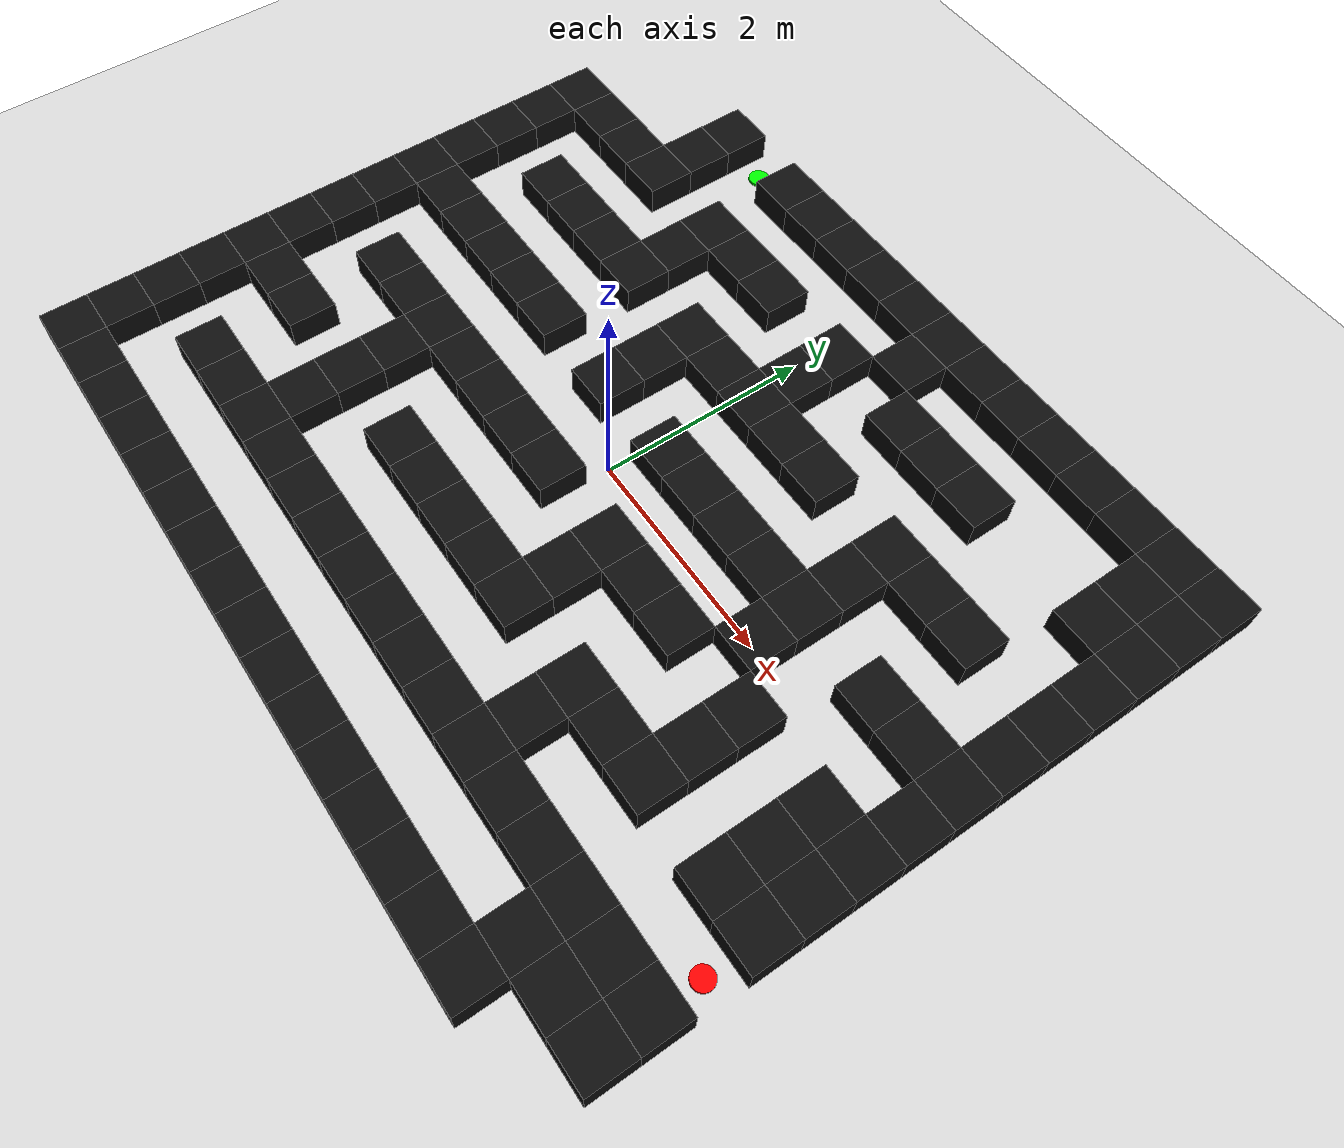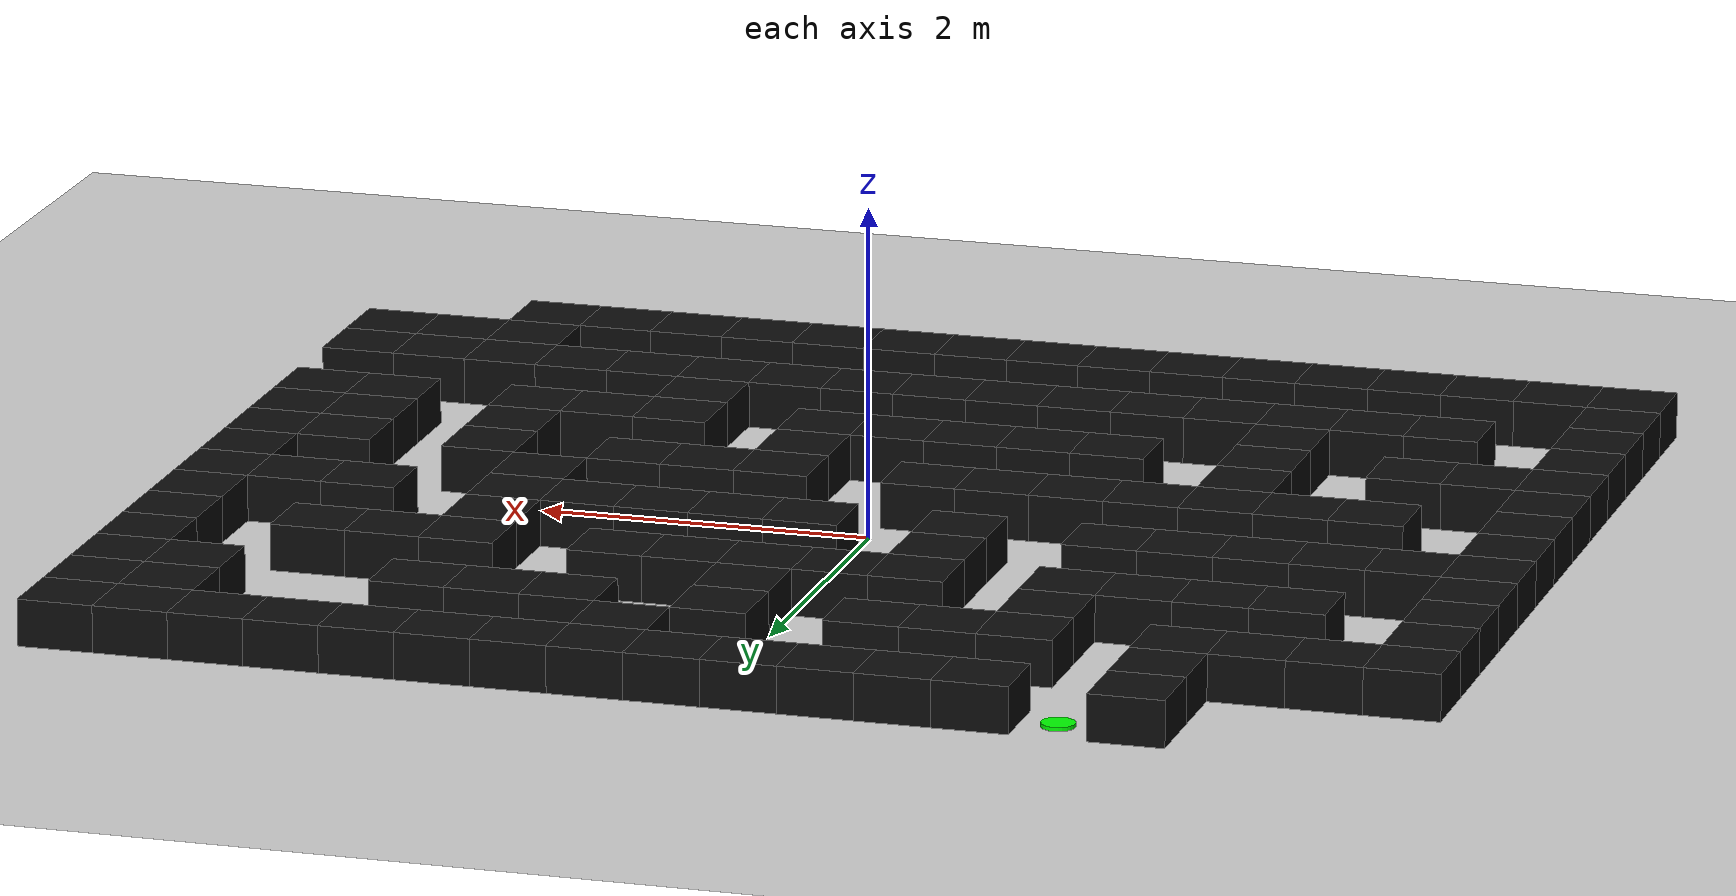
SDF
<?xml version="1.0"?>
<sdf version="1.9">
  <world name="ros2_world">

    <plugin filename="gz-sim-physics-system"
            name="gz::sim::systems::Physics"/>

    <plugin filename="gz-sim-user-commands-system"
            name="gz::sim::systems::UserCommands"/>

    <plugin filename="gz-sim-scene-broadcaster-system"
            name="gz::sim::systems::SceneBroadcaster"/>

    <light type="directional" name="sun">
      <pose>0 0 10 0 0 0</pose>
      <diffuse>0.8 0.8 0.8 1</diffuse>
      <specular>0.2 0.2 0.2 1</specular>
      <direction>-0.5 0.1 -0.9</direction>
    </light>

    <model name="ground_plane">
      <static>true</static>
      <link name="link">
        <collision name="collision">
          <geometry>
            <plane>
              <normal>0 0 1</normal>
              <size>30 30</size>
            </plane>
          </geometry>
        </collision>
        <visual name="visual">
          <geometry>
            <plane>
              <normal>0 0 1</normal>
              <size>30 30</size>
            </plane>
          </geometry>
          <material>
            <ambient>0.82 0.82 0.82 1</ambient>
            <diffuse>0.82 0.82 0.82 1</diffuse>
          </material>
        </visual>
      </link>
    </model>

    <model name="wall_0">
      <static>true</static>
      <pose>-2.475 3.150 0.140 0 0 0</pose>
      <link name="link">
        <collision name="collision">
          <geometry>
            <box>
              <size>0.450 0.450 0.280</size>
            </box>
          </geometry>
        </collision>
        <visual name="visual">
          <geometry>
            <box>
              <size>0.450 0.450 0.280</size>
            </box>
          </geometry>
          <material>
            <ambient>0.05 0.05 0.05 1</ambient>
            <diffuse>0.05 0.05 0.05 1</diffuse>
          </material>
        </visual>
      </link>
    </model>

    <model name="start_marker">
      <static>true</static>
      <pose>-2.025 3.150 0.012 0 0 0</pose>
      <link name="link">
        <visual name="visual">
          <geometry>
            <cylinder>
              <radius>0.099</radius>
              <length>0.024</length>
            </cylinder>
          </geometry>
          <material>
            <ambient>0 1 0 1</ambient>
            <diffuse>0 1 0 1</diffuse>
          </material>
        </visual>
      </link>
    </model>

    <model name="wall_1">
      <static>true</static>
      <pose>-1.575 3.150 0.140 0 0 0</pose>
      <link name="link">
        <collision name="collision">
          <geometry>
            <box>
              <size>0.450 0.450 0.280</size>
            </box>
          </geometry>
        </collision>
        <visual name="visual">
          <geometry>
            <box>
              <size>0.450 0.450 0.280</size>
            </box>
          </geometry>
          <material>
            <ambient>0.05 0.05 0.05 1</ambient>
            <diffuse>0.05 0.05 0.05 1</diffuse>
          </material>
        </visual>
      </link>
    </model>

    <model name="wall_2">
      <static>true</static>
      <pose>-1.125 3.150 0.140 0 0 0</pose>
      <link name="link">
        <collision name="collision">
          <geometry>
            <box>
              <size>0.450 0.450 0.280</size>
            </box>
          </geometry>
        </collision>
        <visual name="visual">
          <geometry>
            <box>
              <size>0.450 0.450 0.280</size>
            </box>
          </geometry>
          <material>
            <ambient>0.05 0.05 0.05 1</ambient>
            <diffuse>0.05 0.05 0.05 1</diffuse>
          </material>
        </visual>
      </link>
    </model>

    <model name="wall_3">
      <static>true</static>
      <pose>-0.675 3.150 0.140 0 0 0</pose>
      <link name="link">
        <collision name="collision">
          <geometry>
            <box>
              <size>0.450 0.450 0.280</size>
            </box>
          </geometry>
        </collision>
        <visual name="visual">
          <geometry>
            <box>
              <size>0.450 0.450 0.280</size>
            </box>
          </geometry>
          <material>
            <ambient>0.05 0.05 0.05 1</ambient>
            <diffuse>0.05 0.05 0.05 1</diffuse>
          </material>
        </visual>
      </link>
    </model>

    <model name="wall_4">
      <static>true</static>
      <pose>-0.225 3.150 0.140 0 0 0</pose>
      <link name="link">
        <collision name="collision">
          <geometry>
            <box>
              <size>0.450 0.450 0.280</size>
            </box>
          </geometry>
        </collision>
        <visual name="visual">
          <geometry>
            <box>
              <size>0.450 0.450 0.280</size>
            </box>
          </geometry>
          <material>
            <ambient>0.05 0.05 0.05 1</ambient>
            <diffuse>0.05 0.05 0.05 1</diffuse>
          </material>
        </visual>
      </link>
    </model>

    <model name="wall_5">
      <static>true</static>
      <pose>0.225 3.150 0.140 0 0 0</pose>
      <link name="link">
        <collision name="collision">
          <geometry>
            <box>
              <size>0.450 0.450 0.280</size>
            </box>
          </geometry>
        </collision>
        <visual name="visual">
          <geometry>
            <box>
              <size>0.450 0.450 0.280</size>
            </box>
          </geometry>
          <material>
            <ambient>0.05 0.05 0.05 1</ambient>
            <diffuse>0.05 0.05 0.05 1</diffuse>
          </material>
        </visual>
      </link>
    </model>

    <model name="wall_6">
      <static>true</static>
      <pose>0.675 3.150 0.140 0 0 0</pose>
      <link name="link">
        <collision name="collision">
          <geometry>
            <box>
              <size>0.450 0.450 0.280</size>
            </box>
          </geometry>
        </collision>
        <visual name="visual">
          <geometry>
            <box>
              <size>0.450 0.450 0.280</size>
            </box>
          </geometry>
          <material>
            <ambient>0.05 0.05 0.05 1</ambient>
            <diffuse>0.05 0.05 0.05 1</diffuse>
          </material>
        </visual>
      </link>
    </model>

    <model name="wall_7">
      <static>true</static>
      <pose>1.125 3.150 0.140 0 0 0</pose>
      <link name="link">
        <collision name="collision">
          <geometry>
            <box>
              <size>0.450 0.450 0.280</size>
            </box>
          </geometry>
        </collision>
        <visual name="visual">
          <geometry>
            <box>
              <size>0.450 0.450 0.280</size>
            </box>
          </geometry>
          <material>
            <ambient>0.05 0.05 0.05 1</ambient>
            <diffuse>0.05 0.05 0.05 1</diffuse>
          </material>
        </visual>
      </link>
    </model>

    <model name="wall_8">
      <static>true</static>
      <pose>1.575 3.150 0.140 0 0 0</pose>
      <link name="link">
        <collision name="collision">
          <geometry>
            <box>
              <size>0.450 0.450 0.280</size>
            </box>
          </geometry>
        </collision>
        <visual name="visual">
          <geometry>
            <box>
              <size>0.450 0.450 0.280</size>
            </box>
          </geometry>
          <material>
            <ambient>0.05 0.05 0.05 1</ambient>
            <diffuse>0.05 0.05 0.05 1</diffuse>
          </material>
        </visual>
      </link>
    </model>

    <model name="wall_9">
      <static>true</static>
      <pose>2.025 3.150 0.140 0 0 0</pose>
      <link name="link">
        <collision name="collision">
          <geometry>
            <box>
              <size>0.450 0.450 0.280</size>
            </box>
          </geometry>
        </collision>
        <visual name="visual">
          <geometry>
            <box>
              <size>0.450 0.450 0.280</size>
            </box>
          </geometry>
          <material>
            <ambient>0.05 0.05 0.05 1</ambient>
            <diffuse>0.05 0.05 0.05 1</diffuse>
          </material>
        </visual>
      </link>
    </model>

    <model name="wall_10">
      <static>true</static>
      <pose>2.475 3.150 0.140 0 0 0</pose>
      <link name="link">
        <collision name="collision">
          <geometry>
            <box>
              <size>0.450 0.450 0.280</size>
            </box>
          </geometry>
        </collision>
        <visual name="visual">
          <geometry>
            <box>
              <size>0.450 0.450 0.280</size>
            </box>
          </geometry>
          <material>
            <ambient>0.05 0.05 0.05 1</ambient>
            <diffuse>0.05 0.05 0.05 1</diffuse>
          </material>
        </visual>
      </link>
    </model>

    <model name="wall_11">
      <static>true</static>
      <pose>2.925 3.150 0.140 0 0 0</pose>
      <link name="link">
        <collision name="collision">
          <geometry>
            <box>
              <size>0.450 0.450 0.280</size>
            </box>
          </geometry>
        </collision>
        <visual name="visual">
          <geometry>
            <box>
              <size>0.450 0.450 0.280</size>
            </box>
          </geometry>
          <material>
            <ambient>0.05 0.05 0.05 1</ambient>
            <diffuse>0.05 0.05 0.05 1</diffuse>
          </material>
        </visual>
      </link>
    </model>

    <model name="wall_12">
      <static>true</static>
      <pose>3.375 3.150 0.140 0 0 0</pose>
      <link name="link">
        <collision name="collision">
          <geometry>
            <box>
              <size>0.450 0.450 0.280</size>
            </box>
          </geometry>
        </collision>
        <visual name="visual">
          <geometry>
            <box>
              <size>0.450 0.450 0.280</size>
            </box>
          </geometry>
          <material>
            <ambient>0.05 0.05 0.05 1</ambient>
            <diffuse>0.05 0.05 0.05 1</diffuse>
          </material>
        </visual>
      </link>
    </model>

    <model name="wall_13">
      <static>true</static>
      <pose>3.825 3.150 0.140 0 0 0</pose>
      <link name="link">
        <collision name="collision">
          <geometry>
            <box>
              <size>0.450 0.450 0.280</size>
            </box>
          </geometry>
        </collision>
        <visual name="visual">
          <geometry>
            <box>
              <size>0.450 0.450 0.280</size>
            </box>
          </geometry>
          <material>
            <ambient>0.05 0.05 0.05 1</ambient>
            <diffuse>0.05 0.05 0.05 1</diffuse>
          </material>
        </visual>
      </link>
    </model>

    <model name="wall_14">
      <static>true</static>
      <pose>-2.475 2.700 0.140 0 0 0</pose>
      <link name="link">
        <collision name="collision">
          <geometry>
            <box>
              <size>0.450 0.450 0.280</size>
            </box>
          </geometry>
        </collision>
        <visual name="visual">
          <geometry>
            <box>
              <size>0.450 0.450 0.280</size>
            </box>
          </geometry>
          <material>
            <ambient>0.05 0.05 0.05 1</ambient>
            <diffuse>0.05 0.05 0.05 1</diffuse>
          </material>
        </visual>
      </link>
    </model>

    <model name="wall_15">
      <static>true</static>
      <pose>0.675 2.700 0.140 0 0 0</pose>
      <link name="link">
        <collision name="collision">
          <geometry>
            <box>
              <size>0.450 0.450 0.280</size>
            </box>
          </geometry>
        </collision>
        <visual name="visual">
          <geometry>
            <box>
              <size>0.450 0.450 0.280</size>
            </box>
          </geometry>
          <material>
            <ambient>0.05 0.05 0.05 1</ambient>
            <diffuse>0.05 0.05 0.05 1</diffuse>
          </material>
        </visual>
      </link>
    </model>

    <model name="wall_16">
      <static>true</static>
      <pose>3.375 2.700 0.140 0 0 0</pose>
      <link name="link">
        <collision name="collision">
          <geometry>
            <box>
              <size>0.450 0.450 0.280</size>
            </box>
          </geometry>
        </collision>
        <visual name="visual">
          <geometry>
            <box>
              <size>0.450 0.450 0.280</size>
            </box>
          </geometry>
          <material>
            <ambient>0.05 0.05 0.05 1</ambient>
            <diffuse>0.05 0.05 0.05 1</diffuse>
          </material>
        </visual>
      </link>
    </model>

    <model name="wall_17">
      <static>true</static>
      <pose>3.825 2.700 0.140 0 0 0</pose>
      <link name="link">
        <collision name="collision">
          <geometry>
            <box>
              <size>0.450 0.450 0.280</size>
            </box>
          </geometry>
        </collision>
        <visual name="visual">
          <geometry>
            <box>
              <size>0.450 0.450 0.280</size>
            </box>
          </geometry>
          <material>
            <ambient>0.05 0.05 0.05 1</ambient>
            <diffuse>0.05 0.05 0.05 1</diffuse>
          </material>
        </visual>
      </link>
    </model>

    <model name="wall_18">
      <static>true</static>
      <pose>-3.825 2.250 0.140 0 0 0</pose>
      <link name="link">
        <collision name="collision">
          <geometry>
            <box>
              <size>0.450 0.450 0.280</size>
            </box>
          </geometry>
        </collision>
        <visual name="visual">
          <geometry>
            <box>
              <size>0.450 0.450 0.280</size>
            </box>
          </geometry>
          <material>
            <ambient>0.05 0.05 0.05 1</ambient>
            <diffuse>0.05 0.05 0.05 1</diffuse>
          </material>
        </visual>
      </link>
    </model>

    <model name="wall_19">
      <static>true</static>
      <pose>-3.375 2.250 0.140 0 0 0</pose>
      <link name="link">
        <collision name="collision">
          <geometry>
            <box>
              <size>0.450 0.450 0.280</size>
            </box>
          </geometry>
        </collision>
        <visual name="visual">
          <geometry>
            <box>
              <size>0.450 0.450 0.280</size>
            </box>
          </geometry>
          <material>
            <ambient>0.05 0.05 0.05 1</ambient>
            <diffuse>0.05 0.05 0.05 1</diffuse>
          </material>
        </visual>
      </link>
    </model>

    <model name="wall_20">
      <static>true</static>
      <pose>-2.925 2.250 0.140 0 0 0</pose>
      <link name="link">
        <collision name="collision">
          <geometry>
            <box>
              <size>0.450 0.450 0.280</size>
            </box>
          </geometry>
        </collision>
        <visual name="visual">
          <geometry>
            <box>
              <size>0.450 0.450 0.280</size>
            </box>
          </geometry>
          <material>
            <ambient>0.05 0.05 0.05 1</ambient>
            <diffuse>0.05 0.05 0.05 1</diffuse>
          </material>
        </visual>
      </link>
    </model>

    <model name="wall_21">
      <static>true</static>
      <pose>-2.475 2.250 0.140 0 0 0</pose>
      <link name="link">
        <collision name="collision">
          <geometry>
            <box>
              <size>0.450 0.450 0.280</size>
            </box>
          </geometry>
        </collision>
        <visual name="visual">
          <geometry>
            <box>
              <size>0.450 0.450 0.280</size>
            </box>
          </geometry>
          <material>
            <ambient>0.05 0.05 0.05 1</ambient>
            <diffuse>0.05 0.05 0.05 1</diffuse>
          </material>
        </visual>
      </link>
    </model>

    <model name="wall_22">
      <static>true</static>
      <pose>-1.575 2.250 0.140 0 0 0</pose>
      <link name="link">
        <collision name="collision">
          <geometry>
            <box>
              <size>0.450 0.450 0.280</size>
            </box>
          </geometry>
        </collision>
        <visual name="visual">
          <geometry>
            <box>
              <size>0.450 0.450 0.280</size>
            </box>
          </geometry>
          <material>
            <ambient>0.05 0.05 0.05 1</ambient>
            <diffuse>0.05 0.05 0.05 1</diffuse>
          </material>
        </visual>
      </link>
    </model>

    <model name="wall_23">
      <static>true</static>
      <pose>-1.125 2.250 0.140 0 0 0</pose>
      <link name="link">
        <collision name="collision">
          <geometry>
            <box>
              <size>0.450 0.450 0.280</size>
            </box>
          </geometry>
        </collision>
        <visual name="visual">
          <geometry>
            <box>
              <size>0.450 0.450 0.280</size>
            </box>
          </geometry>
          <material>
            <ambient>0.05 0.05 0.05 1</ambient>
            <diffuse>0.05 0.05 0.05 1</diffuse>
          </material>
        </visual>
      </link>
    </model>

    <model name="wall_24">
      <static>true</static>
      <pose>-0.675 2.250 0.140 0 0 0</pose>
      <link name="link">
        <collision name="collision">
          <geometry>
            <box>
              <size>0.450 0.450 0.280</size>
            </box>
          </geometry>
        </collision>
        <visual name="visual">
          <geometry>
            <box>
              <size>0.450 0.450 0.280</size>
            </box>
          </geometry>
          <material>
            <ambient>0.05 0.05 0.05 1</ambient>
            <diffuse>0.05 0.05 0.05 1</diffuse>
          </material>
        </visual>
      </link>
    </model>

    <model name="wall_25">
      <static>true</static>
      <pose>0.225 2.250 0.140 0 0 0</pose>
      <link name="link">
        <collision name="collision">
          <geometry>
            <box>
              <size>0.450 0.450 0.280</size>
            </box>
          </geometry>
        </collision>
        <visual name="visual">
          <geometry>
            <box>
              <size>0.450 0.450 0.280</size>
            </box>
          </geometry>
          <material>
            <ambient>0.05 0.05 0.05 1</ambient>
            <diffuse>0.05 0.05 0.05 1</diffuse>
          </material>
        </visual>
      </link>
    </model>

    <model name="wall_26">
      <static>true</static>
      <pose>1.125 2.250 0.140 0 0 0</pose>
      <link name="link">
        <collision name="collision">
          <geometry>
            <box>
              <size>0.450 0.450 0.280</size>
            </box>
          </geometry>
        </collision>
        <visual name="visual">
          <geometry>
            <box>
              <size>0.450 0.450 0.280</size>
            </box>
          </geometry>
          <material>
            <ambient>0.05 0.05 0.05 1</ambient>
            <diffuse>0.05 0.05 0.05 1</diffuse>
          </material>
        </visual>
      </link>
    </model>

    <model name="wall_27">
      <static>true</static>
      <pose>1.575 2.250 0.140 0 0 0</pose>
      <link name="link">
        <collision name="collision">
          <geometry>
            <box>
              <size>0.450 0.450 0.280</size>
            </box>
          </geometry>
        </collision>
        <visual name="visual">
          <geometry>
            <box>
              <size>0.450 0.450 0.280</size>
            </box>
          </geometry>
          <material>
            <ambient>0.05 0.05 0.05 1</ambient>
            <diffuse>0.05 0.05 0.05 1</diffuse>
          </material>
        </visual>
      </link>
    </model>

    <model name="wall_28">
      <static>true</static>
      <pose>2.025 2.250 0.140 0 0 0</pose>
      <link name="link">
        <collision name="collision">
          <geometry>
            <box>
              <size>0.450 0.450 0.280</size>
            </box>
          </geometry>
        </collision>
        <visual name="visual">
          <geometry>
            <box>
              <size>0.450 0.450 0.280</size>
            </box>
          </geometry>
          <material>
            <ambient>0.05 0.05 0.05 1</ambient>
            <diffuse>0.05 0.05 0.05 1</diffuse>
          </material>
        </visual>
      </link>
    </model>

    <model name="wall_29">
      <static>true</static>
      <pose>3.375 2.250 0.140 0 0 0</pose>
      <link name="link">
        <collision name="collision">
          <geometry>
            <box>
              <size>0.450 0.450 0.280</size>
            </box>
          </geometry>
        </collision>
        <visual name="visual">
          <geometry>
            <box>
              <size>0.450 0.450 0.280</size>
            </box>
          </geometry>
          <material>
            <ambient>0.05 0.05 0.05 1</ambient>
            <diffuse>0.05 0.05 0.05 1</diffuse>
          </material>
        </visual>
      </link>
    </model>

    <model name="wall_30">
      <static>true</static>
      <pose>3.825 2.250 0.140 0 0 0</pose>
      <link name="link">
        <collision name="collision">
          <geometry>
            <box>
              <size>0.450 0.450 0.280</size>
            </box>
          </geometry>
        </collision>
        <visual name="visual">
          <geometry>
            <box>
              <size>0.450 0.450 0.280</size>
            </box>
          </geometry>
          <material>
            <ambient>0.05 0.05 0.05 1</ambient>
            <diffuse>0.05 0.05 0.05 1</diffuse>
          </material>
        </visual>
      </link>
    </model>

    <model name="wall_31">
      <static>true</static>
      <pose>-3.825 1.800 0.140 0 0 0</pose>
      <link name="link">
        <collision name="collision">
          <geometry>
            <box>
              <size>0.450 0.450 0.280</size>
            </box>
          </geometry>
        </collision>
        <visual name="visual">
          <geometry>
            <box>
              <size>0.450 0.450 0.280</size>
            </box>
          </geometry>
          <material>
            <ambient>0.05 0.05 0.05 1</ambient>
            <diffuse>0.05 0.05 0.05 1</diffuse>
          </material>
        </visual>
      </link>
    </model>

    <model name="wall_32">
      <static>true</static>
      <pose>-1.575 1.800 0.140 0 0 0</pose>
      <link name="link">
        <collision name="collision">
          <geometry>
            <box>
              <size>0.450 0.450 0.280</size>
            </box>
          </geometry>
        </collision>
        <visual name="visual">
          <geometry>
            <box>
              <size>0.450 0.450 0.280</size>
            </box>
          </geometry>
          <material>
            <ambient>0.05 0.05 0.05 1</ambient>
            <diffuse>0.05 0.05 0.05 1</diffuse>
          </material>
        </visual>
      </link>
    </model>

    <model name="wall_33">
      <static>true</static>
      <pose>0.225 1.800 0.140 0 0 0</pose>
      <link name="link">
        <collision name="collision">
          <geometry>
            <box>
              <size>0.450 0.450 0.280</size>
            </box>
          </geometry>
        </collision>
        <visual name="visual">
          <geometry>
            <box>
              <size>0.450 0.450 0.280</size>
            </box>
          </geometry>
          <material>
            <ambient>0.05 0.05 0.05 1</ambient>
            <diffuse>0.05 0.05 0.05 1</diffuse>
          </material>
        </visual>
      </link>
    </model>

    <model name="wall_34">
      <static>true</static>
      <pose>3.825 1.800 0.140 0 0 0</pose>
      <link name="link">
        <collision name="collision">
          <geometry>
            <box>
              <size>0.450 0.450 0.280</size>
            </box>
          </geometry>
        </collision>
        <visual name="visual">
          <geometry>
            <box>
              <size>0.450 0.450 0.280</size>
            </box>
          </geometry>
          <material>
            <ambient>0.05 0.05 0.05 1</ambient>
            <diffuse>0.05 0.05 0.05 1</diffuse>
          </material>
        </visual>
      </link>
    </model>

    <model name="wall_35">
      <static>true</static>
      <pose>-3.825 1.350 0.140 0 0 0</pose>
      <link name="link">
        <collision name="collision">
          <geometry>
            <box>
              <size>0.450 0.450 0.280</size>
            </box>
          </geometry>
        </collision>
        <visual name="visual">
          <geometry>
            <box>
              <size>0.450 0.450 0.280</size>
            </box>
          </geometry>
          <material>
            <ambient>0.05 0.05 0.05 1</ambient>
            <diffuse>0.05 0.05 0.05 1</diffuse>
          </material>
        </visual>
      </link>
    </model>

    <model name="wall_36">
      <static>true</static>
      <pose>-2.925 1.350 0.140 0 0 0</pose>
      <link name="link">
        <collision name="collision">
          <geometry>
            <box>
              <size>0.450 0.450 0.280</size>
            </box>
          </geometry>
        </collision>
        <visual name="visual">
          <geometry>
            <box>
              <size>0.450 0.450 0.280</size>
            </box>
          </geometry>
          <material>
            <ambient>0.05 0.05 0.05 1</ambient>
            <diffuse>0.05 0.05 0.05 1</diffuse>
          </material>
        </visual>
      </link>
    </model>

    <model name="wall_37">
      <static>true</static>
      <pose>-2.475 1.350 0.140 0 0 0</pose>
      <link name="link">
        <collision name="collision">
          <geometry>
            <box>
              <size>0.450 0.450 0.280</size>
            </box>
          </geometry>
        </collision>
        <visual name="visual">
          <geometry>
            <box>
              <size>0.450 0.450 0.280</size>
            </box>
          </geometry>
          <material>
            <ambient>0.05 0.05 0.05 1</ambient>
            <diffuse>0.05 0.05 0.05 1</diffuse>
          </material>
        </visual>
      </link>
    </model>

    <model name="wall_38">
      <static>true</static>
      <pose>-2.025 1.350 0.140 0 0 0</pose>
      <link name="link">
        <collision name="collision">
          <geometry>
            <box>
              <size>0.450 0.450 0.280</size>
            </box>
          </geometry>
        </collision>
        <visual name="visual">
          <geometry>
            <box>
              <size>0.450 0.450 0.280</size>
            </box>
          </geometry>
          <material>
            <ambient>0.05 0.05 0.05 1</ambient>
            <diffuse>0.05 0.05 0.05 1</diffuse>
          </material>
        </visual>
      </link>
    </model>

    <model name="wall_39">
      <static>true</static>
      <pose>-1.575 1.350 0.140 0 0 0</pose>
      <link name="link">
        <collision name="collision">
          <geometry>
            <box>
              <size>0.450 0.450 0.280</size>
            </box>
          </geometry>
        </collision>
        <visual name="visual">
          <geometry>
            <box>
              <size>0.450 0.450 0.280</size>
            </box>
          </geometry>
          <material>
            <ambient>0.05 0.05 0.05 1</ambient>
            <diffuse>0.05 0.05 0.05 1</diffuse>
          </material>
        </visual>
      </link>
    </model>

    <model name="wall_40">
      <static>true</static>
      <pose>-0.675 1.350 0.140 0 0 0</pose>
      <link name="link">
        <collision name="collision">
          <geometry>
            <box>
              <size>0.450 0.450 0.280</size>
            </box>
          </geometry>
        </collision>
        <visual name="visual">
          <geometry>
            <box>
              <size>0.450 0.450 0.280</size>
            </box>
          </geometry>
          <material>
            <ambient>0.05 0.05 0.05 1</ambient>
            <diffuse>0.05 0.05 0.05 1</diffuse>
          </material>
        </visual>
      </link>
    </model>

    <model name="wall_41">
      <static>true</static>
      <pose>-0.225 1.350 0.140 0 0 0</pose>
      <link name="link">
        <collision name="collision">
          <geometry>
            <box>
              <size>0.450 0.450 0.280</size>
            </box>
          </geometry>
        </collision>
        <visual name="visual">
          <geometry>
            <box>
              <size>0.450 0.450 0.280</size>
            </box>
          </geometry>
          <material>
            <ambient>0.05 0.05 0.05 1</ambient>
            <diffuse>0.05 0.05 0.05 1</diffuse>
          </material>
        </visual>
      </link>
    </model>

    <model name="wall_42">
      <static>true</static>
      <pose>0.225 1.350 0.140 0 0 0</pose>
      <link name="link">
        <collision name="collision">
          <geometry>
            <box>
              <size>0.450 0.450 0.280</size>
            </box>
          </geometry>
        </collision>
        <visual name="visual">
          <geometry>
            <box>
              <size>0.450 0.450 0.280</size>
            </box>
          </geometry>
          <material>
            <ambient>0.05 0.05 0.05 1</ambient>
            <diffuse>0.05 0.05 0.05 1</diffuse>
          </material>
        </visual>
      </link>
    </model>

    <model name="wall_43">
      <static>true</static>
      <pose>0.675 1.350 0.140 0 0 0</pose>
      <link name="link">
        <collision name="collision">
          <geometry>
            <box>
              <size>0.450 0.450 0.280</size>
            </box>
          </geometry>
        </collision>
        <visual name="visual">
          <geometry>
            <box>
              <size>0.450 0.450 0.280</size>
            </box>
          </geometry>
          <material>
            <ambient>0.05 0.05 0.05 1</ambient>
            <diffuse>0.05 0.05 0.05 1</diffuse>
          </material>
        </visual>
      </link>
    </model>

    <model name="wall_44">
      <static>true</static>
      <pose>1.125 1.350 0.140 0 0 0</pose>
      <link name="link">
        <collision name="collision">
          <geometry>
            <box>
              <size>0.450 0.450 0.280</size>
            </box>
          </geometry>
        </collision>
        <visual name="visual">
          <geometry>
            <box>
              <size>0.450 0.450 0.280</size>
            </box>
          </geometry>
          <material>
            <ambient>0.05 0.05 0.05 1</ambient>
            <diffuse>0.05 0.05 0.05 1</diffuse>
          </material>
        </visual>
      </link>
    </model>

    <model name="wall_45">
      <static>true</static>
      <pose>2.025 1.350 0.140 0 0 0</pose>
      <link name="link">
        <collision name="collision">
          <geometry>
            <box>
              <size>0.450 0.450 0.280</size>
            </box>
          </geometry>
        </collision>
        <visual name="visual">
          <geometry>
            <box>
              <size>0.450 0.450 0.280</size>
            </box>
          </geometry>
          <material>
            <ambient>0.05 0.05 0.05 1</ambient>
            <diffuse>0.05 0.05 0.05 1</diffuse>
          </material>
        </visual>
      </link>
    </model>

    <model name="wall_46">
      <static>true</static>
      <pose>2.475 1.350 0.140 0 0 0</pose>
      <link name="link">
        <collision name="collision">
          <geometry>
            <box>
              <size>0.450 0.450 0.280</size>
            </box>
          </geometry>
        </collision>
        <visual name="visual">
          <geometry>
            <box>
              <size>0.450 0.450 0.280</size>
            </box>
          </geometry>
          <material>
            <ambient>0.05 0.05 0.05 1</ambient>
            <diffuse>0.05 0.05 0.05 1</diffuse>
          </material>
        </visual>
      </link>
    </model>

    <model name="wall_47">
      <static>true</static>
      <pose>2.925 1.350 0.140 0 0 0</pose>
      <link name="link">
        <collision name="collision">
          <geometry>
            <box>
              <size>0.450 0.450 0.280</size>
            </box>
          </geometry>
        </collision>
        <visual name="visual">
          <geometry>
            <box>
              <size>0.450 0.450 0.280</size>
            </box>
          </geometry>
          <material>
            <ambient>0.05 0.05 0.05 1</ambient>
            <diffuse>0.05 0.05 0.05 1</diffuse>
          </material>
        </visual>
      </link>
    </model>

    <model name="wall_48">
      <static>true</static>
      <pose>3.825 1.350 0.140 0 0 0</pose>
      <link name="link">
        <collision name="collision">
          <geometry>
            <box>
              <size>0.450 0.450 0.280</size>
            </box>
          </geometry>
        </collision>
        <visual name="visual">
          <geometry>
            <box>
              <size>0.450 0.450 0.280</size>
            </box>
          </geometry>
          <material>
            <ambient>0.05 0.05 0.05 1</ambient>
            <diffuse>0.05 0.05 0.05 1</diffuse>
          </material>
        </visual>
      </link>
    </model>

    <model name="wall_49">
      <static>true</static>
      <pose>-3.825 0.900 0.140 0 0 0</pose>
      <link name="link">
        <collision name="collision">
          <geometry>
            <box>
              <size>0.450 0.450 0.280</size>
            </box>
          </geometry>
        </collision>
        <visual name="visual">
          <geometry>
            <box>
              <size>0.450 0.450 0.280</size>
            </box>
          </geometry>
          <material>
            <ambient>0.05 0.05 0.05 1</ambient>
            <diffuse>0.05 0.05 0.05 1</diffuse>
          </material>
        </visual>
      </link>
    </model>

    <model name="wall_50">
      <static>true</static>
      <pose>-0.675 0.900 0.140 0 0 0</pose>
      <link name="link">
        <collision name="collision">
          <geometry>
            <box>
              <size>0.450 0.450 0.280</size>
            </box>
          </geometry>
        </collision>
        <visual name="visual">
          <geometry>
            <box>
              <size>0.450 0.450 0.280</size>
            </box>
          </geometry>
          <material>
            <ambient>0.05 0.05 0.05 1</ambient>
            <diffuse>0.05 0.05 0.05 1</diffuse>
          </material>
        </visual>
      </link>
    </model>

    <model name="wall_51">
      <static>true</static>
      <pose>2.025 0.900 0.140 0 0 0</pose>
      <link name="link">
        <collision name="collision">
          <geometry>
            <box>
              <size>0.450 0.450 0.280</size>
            </box>
          </geometry>
        </collision>
        <visual name="visual">
          <geometry>
            <box>
              <size>0.450 0.450 0.280</size>
            </box>
          </geometry>
          <material>
            <ambient>0.05 0.05 0.05 1</ambient>
            <diffuse>0.05 0.05 0.05 1</diffuse>
          </material>
        </visual>
      </link>
    </model>

    <model name="wall_52">
      <static>true</static>
      <pose>3.825 0.900 0.140 0 0 0</pose>
      <link name="link">
        <collision name="collision">
          <geometry>
            <box>
              <size>0.450 0.450 0.280</size>
            </box>
          </geometry>
        </collision>
        <visual name="visual">
          <geometry>
            <box>
              <size>0.450 0.450 0.280</size>
            </box>
          </geometry>
          <material>
            <ambient>0.05 0.05 0.05 1</ambient>
            <diffuse>0.05 0.05 0.05 1</diffuse>
          </material>
        </visual>
      </link>
    </model>

    <model name="wall_53">
      <static>true</static>
      <pose>-3.825 0.450 0.140 0 0 0</pose>
      <link name="link">
        <collision name="collision">
          <geometry>
            <box>
              <size>0.450 0.450 0.280</size>
            </box>
          </geometry>
        </collision>
        <visual name="visual">
          <geometry>
            <box>
              <size>0.450 0.450 0.280</size>
            </box>
          </geometry>
          <material>
            <ambient>0.05 0.05 0.05 1</ambient>
            <diffuse>0.05 0.05 0.05 1</diffuse>
          </material>
        </visual>
      </link>
    </model>

    <model name="wall_54">
      <static>true</static>
      <pose>-3.375 0.450 0.140 0 0 0</pose>
      <link name="link">
        <collision name="collision">
          <geometry>
            <box>
              <size>0.450 0.450 0.280</size>
            </box>
          </geometry>
        </collision>
        <visual name="visual">
          <geometry>
            <box>
              <size>0.450 0.450 0.280</size>
            </box>
          </geometry>
          <material>
            <ambient>0.05 0.05 0.05 1</ambient>
            <diffuse>0.05 0.05 0.05 1</diffuse>
          </material>
        </visual>
      </link>
    </model>

    <model name="wall_55">
      <static>true</static>
      <pose>-2.925 0.450 0.140 0 0 0</pose>
      <link name="link">
        <collision name="collision">
          <geometry>
            <box>
              <size>0.450 0.450 0.280</size>
            </box>
          </geometry>
        </collision>
        <visual name="visual">
          <geometry>
            <box>
              <size>0.450 0.450 0.280</size>
            </box>
          </geometry>
          <material>
            <ambient>0.05 0.05 0.05 1</ambient>
            <diffuse>0.05 0.05 0.05 1</diffuse>
          </material>
        </visual>
      </link>
    </model>

    <model name="wall_56">
      <static>true</static>
      <pose>-2.475 0.450 0.140 0 0 0</pose>
      <link name="link">
        <collision name="collision">
          <geometry>
            <box>
              <size>0.450 0.450 0.280</size>
            </box>
          </geometry>
        </collision>
        <visual name="visual">
          <geometry>
            <box>
              <size>0.450 0.450 0.280</size>
            </box>
          </geometry>
          <material>
            <ambient>0.05 0.05 0.05 1</ambient>
            <diffuse>0.05 0.05 0.05 1</diffuse>
          </material>
        </visual>
      </link>
    </model>

    <model name="wall_57">
      <static>true</static>
      <pose>-2.025 0.450 0.140 0 0 0</pose>
      <link name="link">
        <collision name="collision">
          <geometry>
            <box>
              <size>0.450 0.450 0.280</size>
            </box>
          </geometry>
        </collision>
        <visual name="visual">
          <geometry>
            <box>
              <size>0.450 0.450 0.280</size>
            </box>
          </geometry>
          <material>
            <ambient>0.05 0.05 0.05 1</ambient>
            <diffuse>0.05 0.05 0.05 1</diffuse>
          </material>
        </visual>
      </link>
    </model>

    <model name="wall_58">
      <static>true</static>
      <pose>-1.575 0.450 0.140 0 0 0</pose>
      <link name="link">
        <collision name="collision">
          <geometry>
            <box>
              <size>0.450 0.450 0.280</size>
            </box>
          </geometry>
        </collision>
        <visual name="visual">
          <geometry>
            <box>
              <size>0.450 0.450 0.280</size>
            </box>
          </geometry>
          <material>
            <ambient>0.05 0.05 0.05 1</ambient>
            <diffuse>0.05 0.05 0.05 1</diffuse>
          </material>
        </visual>
      </link>
    </model>

    <model name="wall_59">
      <static>true</static>
      <pose>-0.675 0.450 0.140 0 0 0</pose>
      <link name="link">
        <collision name="collision">
          <geometry>
            <box>
              <size>0.450 0.450 0.280</size>
            </box>
          </geometry>
        </collision>
        <visual name="visual">
          <geometry>
            <box>
              <size>0.450 0.450 0.280</size>
            </box>
          </geometry>
          <material>
            <ambient>0.05 0.05 0.05 1</ambient>
            <diffuse>0.05 0.05 0.05 1</diffuse>
          </material>
        </visual>
      </link>
    </model>

    <model name="wall_60">
      <static>true</static>
      <pose>0.225 0.450 0.140 0 0 0</pose>
      <link name="link">
        <collision name="collision">
          <geometry>
            <box>
              <size>0.450 0.450 0.280</size>
            </box>
          </geometry>
        </collision>
        <visual name="visual">
          <geometry>
            <box>
              <size>0.450 0.450 0.280</size>
            </box>
          </geometry>
          <material>
            <ambient>0.05 0.05 0.05 1</ambient>
            <diffuse>0.05 0.05 0.05 1</diffuse>
          </material>
        </visual>
      </link>
    </model>

    <model name="wall_61">
      <static>true</static>
      <pose>0.675 0.450 0.140 0 0 0</pose>
      <link name="link">
        <collision name="collision">
          <geometry>
            <box>
              <size>0.450 0.450 0.280</size>
            </box>
          </geometry>
        </collision>
        <visual name="visual">
          <geometry>
            <box>
              <size>0.450 0.450 0.280</size>
            </box>
          </geometry>
          <material>
            <ambient>0.05 0.05 0.05 1</ambient>
            <diffuse>0.05 0.05 0.05 1</diffuse>
          </material>
        </visual>
      </link>
    </model>

    <model name="wall_62">
      <static>true</static>
      <pose>1.125 0.450 0.140 0 0 0</pose>
      <link name="link">
        <collision name="collision">
          <geometry>
            <box>
              <size>0.450 0.450 0.280</size>
            </box>
          </geometry>
        </collision>
        <visual name="visual">
          <geometry>
            <box>
              <size>0.450 0.450 0.280</size>
            </box>
          </geometry>
          <material>
            <ambient>0.05 0.05 0.05 1</ambient>
            <diffuse>0.05 0.05 0.05 1</diffuse>
          </material>
        </visual>
      </link>
    </model>

    <model name="wall_63">
      <static>true</static>
      <pose>1.575 0.450 0.140 0 0 0</pose>
      <link name="link">
        <collision name="collision">
          <geometry>
            <box>
              <size>0.450 0.450 0.280</size>
            </box>
          </geometry>
        </collision>
        <visual name="visual">
          <geometry>
            <box>
              <size>0.450 0.450 0.280</size>
            </box>
          </geometry>
          <material>
            <ambient>0.05 0.05 0.05 1</ambient>
            <diffuse>0.05 0.05 0.05 1</diffuse>
          </material>
        </visual>
      </link>
    </model>

    <model name="wall_64">
      <static>true</static>
      <pose>2.025 0.450 0.140 0 0 0</pose>
      <link name="link">
        <collision name="collision">
          <geometry>
            <box>
              <size>0.450 0.450 0.280</size>
            </box>
          </geometry>
        </collision>
        <visual name="visual">
          <geometry>
            <box>
              <size>0.450 0.450 0.280</size>
            </box>
          </geometry>
          <material>
            <ambient>0.05 0.05 0.05 1</ambient>
            <diffuse>0.05 0.05 0.05 1</diffuse>
          </material>
        </visual>
      </link>
    </model>

    <model name="wall_65">
      <static>true</static>
      <pose>2.925 0.450 0.140 0 0 0</pose>
      <link name="link">
        <collision name="collision">
          <geometry>
            <box>
              <size>0.450 0.450 0.280</size>
            </box>
          </geometry>
        </collision>
        <visual name="visual">
          <geometry>
            <box>
              <size>0.450 0.450 0.280</size>
            </box>
          </geometry>
          <material>
            <ambient>0.05 0.05 0.05 1</ambient>
            <diffuse>0.05 0.05 0.05 1</diffuse>
          </material>
        </visual>
      </link>
    </model>

    <model name="wall_66">
      <static>true</static>
      <pose>3.375 0.450 0.140 0 0 0</pose>
      <link name="link">
        <collision name="collision">
          <geometry>
            <box>
              <size>0.450 0.450 0.280</size>
            </box>
          </geometry>
        </collision>
        <visual name="visual">
          <geometry>
            <box>
              <size>0.450 0.450 0.280</size>
            </box>
          </geometry>
          <material>
            <ambient>0.05 0.05 0.05 1</ambient>
            <diffuse>0.05 0.05 0.05 1</diffuse>
          </material>
        </visual>
      </link>
    </model>

    <model name="wall_67">
      <static>true</static>
      <pose>3.825 0.450 0.140 0 0 0</pose>
      <link name="link">
        <collision name="collision">
          <geometry>
            <box>
              <size>0.450 0.450 0.280</size>
            </box>
          </geometry>
        </collision>
        <visual name="visual">
          <geometry>
            <box>
              <size>0.450 0.450 0.280</size>
            </box>
          </geometry>
          <material>
            <ambient>0.05 0.05 0.05 1</ambient>
            <diffuse>0.05 0.05 0.05 1</diffuse>
          </material>
        </visual>
      </link>
    </model>

    <model name="wall_68">
      <static>true</static>
      <pose>-3.825 0.000 0.140 0 0 0</pose>
      <link name="link">
        <collision name="collision">
          <geometry>
            <box>
              <size>0.450 0.450 0.280</size>
            </box>
          </geometry>
        </collision>
        <visual name="visual">
          <geometry>
            <box>
              <size>0.450 0.450 0.280</size>
            </box>
          </geometry>
          <material>
            <ambient>0.05 0.05 0.05 1</ambient>
            <diffuse>0.05 0.05 0.05 1</diffuse>
          </material>
        </visual>
      </link>
    </model>

    <model name="wall_69">
      <static>true</static>
      <pose>2.025 0.000 0.140 0 0 0</pose>
      <link name="link">
        <collision name="collision">
          <geometry>
            <box>
              <size>0.450 0.450 0.280</size>
            </box>
          </geometry>
        </collision>
        <visual name="visual">
          <geometry>
            <box>
              <size>0.450 0.450 0.280</size>
            </box>
          </geometry>
          <material>
            <ambient>0.05 0.05 0.05 1</ambient>
            <diffuse>0.05 0.05 0.05 1</diffuse>
          </material>
        </visual>
      </link>
    </model>

    <model name="wall_70">
      <static>true</static>
      <pose>3.825 0.000 0.140 0 0 0</pose>
      <link name="link">
        <collision name="collision">
          <geometry>
            <box>
              <size>0.450 0.450 0.280</size>
            </box>
          </geometry>
        </collision>
        <visual name="visual">
          <geometry>
            <box>
              <size>0.450 0.450 0.280</size>
            </box>
          </geometry>
          <material>
            <ambient>0.05 0.05 0.05 1</ambient>
            <diffuse>0.05 0.05 0.05 1</diffuse>
          </material>
        </visual>
      </link>
    </model>

    <model name="wall_71">
      <static>true</static>
      <pose>-3.825 -0.450 0.140 0 0 0</pose>
      <link name="link">
        <collision name="collision">
          <geometry>
            <box>
              <size>0.450 0.450 0.280</size>
            </box>
          </geometry>
        </collision>
        <visual name="visual">
          <geometry>
            <box>
              <size>0.450 0.450 0.280</size>
            </box>
          </geometry>
          <material>
            <ambient>0.05 0.05 0.05 1</ambient>
            <diffuse>0.05 0.05 0.05 1</diffuse>
          </material>
        </visual>
      </link>
    </model>

    <model name="wall_72">
      <static>true</static>
      <pose>-2.925 -0.450 0.140 0 0 0</pose>
      <link name="link">
        <collision name="collision">
          <geometry>
            <box>
              <size>0.450 0.450 0.280</size>
            </box>
          </geometry>
        </collision>
        <visual name="visual">
          <geometry>
            <box>
              <size>0.450 0.450 0.280</size>
            </box>
          </geometry>
          <material>
            <ambient>0.05 0.05 0.05 1</ambient>
            <diffuse>0.05 0.05 0.05 1</diffuse>
          </material>
        </visual>
      </link>
    </model>

    <model name="wall_73">
      <static>true</static>
      <pose>-2.475 -0.450 0.140 0 0 0</pose>
      <link name="link">
        <collision name="collision">
          <geometry>
            <box>
              <size>0.450 0.450 0.280</size>
            </box>
          </geometry>
        </collision>
        <visual name="visual">
          <geometry>
            <box>
              <size>0.450 0.450 0.280</size>
            </box>
          </geometry>
          <material>
            <ambient>0.05 0.05 0.05 1</ambient>
            <diffuse>0.05 0.05 0.05 1</diffuse>
          </material>
        </visual>
      </link>
    </model>

    <model name="wall_74">
      <static>true</static>
      <pose>-2.025 -0.450 0.140 0 0 0</pose>
      <link name="link">
        <collision name="collision">
          <geometry>
            <box>
              <size>0.450 0.450 0.280</size>
            </box>
          </geometry>
        </collision>
        <visual name="visual">
          <geometry>
            <box>
              <size>0.450 0.450 0.280</size>
            </box>
          </geometry>
          <material>
            <ambient>0.05 0.05 0.05 1</ambient>
            <diffuse>0.05 0.05 0.05 1</diffuse>
          </material>
        </visual>
      </link>
    </model>

    <model name="wall_75">
      <static>true</static>
      <pose>-1.575 -0.450 0.140 0 0 0</pose>
      <link name="link">
        <collision name="collision">
          <geometry>
            <box>
              <size>0.450 0.450 0.280</size>
            </box>
          </geometry>
        </collision>
        <visual name="visual">
          <geometry>
            <box>
              <size>0.450 0.450 0.280</size>
            </box>
          </geometry>
          <material>
            <ambient>0.05 0.05 0.05 1</ambient>
            <diffuse>0.05 0.05 0.05 1</diffuse>
          </material>
        </visual>
      </link>
    </model>

    <model name="wall_76">
      <static>true</static>
      <pose>-1.125 -0.450 0.140 0 0 0</pose>
      <link name="link">
        <collision name="collision">
          <geometry>
            <box>
              <size>0.450 0.450 0.280</size>
            </box>
          </geometry>
        </collision>
        <visual name="visual">
          <geometry>
            <box>
              <size>0.450 0.450 0.280</size>
            </box>
          </geometry>
          <material>
            <ambient>0.05 0.05 0.05 1</ambient>
            <diffuse>0.05 0.05 0.05 1</diffuse>
          </material>
        </visual>
      </link>
    </model>

    <model name="wall_77">
      <static>true</static>
      <pose>-0.675 -0.450 0.140 0 0 0</pose>
      <link name="link">
        <collision name="collision">
          <geometry>
            <box>
              <size>0.450 0.450 0.280</size>
            </box>
          </geometry>
        </collision>
        <visual name="visual">
          <geometry>
            <box>
              <size>0.450 0.450 0.280</size>
            </box>
          </geometry>
          <material>
            <ambient>0.05 0.05 0.05 1</ambient>
            <diffuse>0.05 0.05 0.05 1</diffuse>
          </material>
        </visual>
      </link>
    </model>

    <model name="wall_78">
      <static>true</static>
      <pose>-0.225 -0.450 0.140 0 0 0</pose>
      <link name="link">
        <collision name="collision">
          <geometry>
            <box>
              <size>0.450 0.450 0.280</size>
            </box>
          </geometry>
        </collision>
        <visual name="visual">
          <geometry>
            <box>
              <size>0.450 0.450 0.280</size>
            </box>
          </geometry>
          <material>
            <ambient>0.05 0.05 0.05 1</ambient>
            <diffuse>0.05 0.05 0.05 1</diffuse>
          </material>
        </visual>
      </link>
    </model>

    <model name="wall_79">
      <static>true</static>
      <pose>0.675 -0.450 0.140 0 0 0</pose>
      <link name="link">
        <collision name="collision">
          <geometry>
            <box>
              <size>0.450 0.450 0.280</size>
            </box>
          </geometry>
        </collision>
        <visual name="visual">
          <geometry>
            <box>
              <size>0.450 0.450 0.280</size>
            </box>
          </geometry>
          <material>
            <ambient>0.05 0.05 0.05 1</ambient>
            <diffuse>0.05 0.05 0.05 1</diffuse>
          </material>
        </visual>
      </link>
    </model>

    <model name="wall_80">
      <static>true</static>
      <pose>1.125 -0.450 0.140 0 0 0</pose>
      <link name="link">
        <collision name="collision">
          <geometry>
            <box>
              <size>0.450 0.450 0.280</size>
            </box>
          </geometry>
        </collision>
        <visual name="visual">
          <geometry>
            <box>
              <size>0.450 0.450 0.280</size>
            </box>
          </geometry>
          <material>
            <ambient>0.05 0.05 0.05 1</ambient>
            <diffuse>0.05 0.05 0.05 1</diffuse>
          </material>
        </visual>
      </link>
    </model>

    <model name="wall_81">
      <static>true</static>
      <pose>1.575 -0.450 0.140 0 0 0</pose>
      <link name="link">
        <collision name="collision">
          <geometry>
            <box>
              <size>0.450 0.450 0.280</size>
            </box>
          </geometry>
        </collision>
        <visual name="visual">
          <geometry>
            <box>
              <size>0.450 0.450 0.280</size>
            </box>
          </geometry>
          <material>
            <ambient>0.05 0.05 0.05 1</ambient>
            <diffuse>0.05 0.05 0.05 1</diffuse>
          </material>
        </visual>
      </link>
    </model>

    <model name="wall_82">
      <static>true</static>
      <pose>2.475 -0.450 0.140 0 0 0</pose>
      <link name="link">
        <collision name="collision">
          <geometry>
            <box>
              <size>0.450 0.450 0.280</size>
            </box>
          </geometry>
        </collision>
        <visual name="visual">
          <geometry>
            <box>
              <size>0.450 0.450 0.280</size>
            </box>
          </geometry>
          <material>
            <ambient>0.05 0.05 0.05 1</ambient>
            <diffuse>0.05 0.05 0.05 1</diffuse>
          </material>
        </visual>
      </link>
    </model>

    <model name="wall_83">
      <static>true</static>
      <pose>3.375 -0.450 0.140 0 0 0</pose>
      <link name="link">
        <collision name="collision">
          <geometry>
            <box>
              <size>0.450 0.450 0.280</size>
            </box>
          </geometry>
        </collision>
        <visual name="visual">
          <geometry>
            <box>
              <size>0.450 0.450 0.280</size>
            </box>
          </geometry>
          <material>
            <ambient>0.05 0.05 0.05 1</ambient>
            <diffuse>0.05 0.05 0.05 1</diffuse>
          </material>
        </visual>
      </link>
    </model>

    <model name="wall_84">
      <static>true</static>
      <pose>3.825 -0.450 0.140 0 0 0</pose>
      <link name="link">
        <collision name="collision">
          <geometry>
            <box>
              <size>0.450 0.450 0.280</size>
            </box>
          </geometry>
        </collision>
        <visual name="visual">
          <geometry>
            <box>
              <size>0.450 0.450 0.280</size>
            </box>
          </geometry>
          <material>
            <ambient>0.05 0.05 0.05 1</ambient>
            <diffuse>0.05 0.05 0.05 1</diffuse>
          </material>
        </visual>
      </link>
    </model>

    <model name="wall_85">
      <static>true</static>
      <pose>-3.825 -0.900 0.140 0 0 0</pose>
      <link name="link">
        <collision name="collision">
          <geometry>
            <box>
              <size>0.450 0.450 0.280</size>
            </box>
          </geometry>
        </collision>
        <visual name="visual">
          <geometry>
            <box>
              <size>0.450 0.450 0.280</size>
            </box>
          </geometry>
          <material>
            <ambient>0.05 0.05 0.05 1</ambient>
            <diffuse>0.05 0.05 0.05 1</diffuse>
          </material>
        </visual>
      </link>
    </model>

    <model name="wall_86">
      <static>true</static>
      <pose>-2.025 -0.900 0.140 0 0 0</pose>
      <link name="link">
        <collision name="collision">
          <geometry>
            <box>
              <size>0.450 0.450 0.280</size>
            </box>
          </geometry>
        </collision>
        <visual name="visual">
          <geometry>
            <box>
              <size>0.450 0.450 0.280</size>
            </box>
          </geometry>
          <material>
            <ambient>0.05 0.05 0.05 1</ambient>
            <diffuse>0.05 0.05 0.05 1</diffuse>
          </material>
        </visual>
      </link>
    </model>

    <model name="wall_87">
      <static>true</static>
      <pose>0.675 -0.900 0.140 0 0 0</pose>
      <link name="link">
        <collision name="collision">
          <geometry>
            <box>
              <size>0.450 0.450 0.280</size>
            </box>
          </geometry>
        </collision>
        <visual name="visual">
          <geometry>
            <box>
              <size>0.450 0.450 0.280</size>
            </box>
          </geometry>
          <material>
            <ambient>0.05 0.05 0.05 1</ambient>
            <diffuse>0.05 0.05 0.05 1</diffuse>
          </material>
        </visual>
      </link>
    </model>

    <model name="wall_88">
      <static>true</static>
      <pose>2.475 -0.900 0.140 0 0 0</pose>
      <link name="link">
        <collision name="collision">
          <geometry>
            <box>
              <size>0.450 0.450 0.280</size>
            </box>
          </geometry>
        </collision>
        <visual name="visual">
          <geometry>
            <box>
              <size>0.450 0.450 0.280</size>
            </box>
          </geometry>
          <material>
            <ambient>0.05 0.05 0.05 1</ambient>
            <diffuse>0.05 0.05 0.05 1</diffuse>
          </material>
        </visual>
      </link>
    </model>

    <model name="wall_89">
      <static>true</static>
      <pose>3.375 -0.900 0.140 0 0 0</pose>
      <link name="link">
        <collision name="collision">
          <geometry>
            <box>
              <size>0.450 0.450 0.280</size>
            </box>
          </geometry>
        </collision>
        <visual name="visual">
          <geometry>
            <box>
              <size>0.450 0.450 0.280</size>
            </box>
          </geometry>
          <material>
            <ambient>0.05 0.05 0.05 1</ambient>
            <diffuse>0.05 0.05 0.05 1</diffuse>
          </material>
        </visual>
      </link>
    </model>

    <model name="wall_90">
      <static>true</static>
      <pose>3.825 -0.900 0.140 0 0 0</pose>
      <link name="link">
        <collision name="collision">
          <geometry>
            <box>
              <size>0.450 0.450 0.280</size>
            </box>
          </geometry>
        </collision>
        <visual name="visual">
          <geometry>
            <box>
              <size>0.450 0.450 0.280</size>
            </box>
          </geometry>
          <material>
            <ambient>0.05 0.05 0.05 1</ambient>
            <diffuse>0.05 0.05 0.05 1</diffuse>
          </material>
        </visual>
      </link>
    </model>

    <model name="wall_91">
      <static>true</static>
      <pose>-3.825 -1.350 0.140 0 0 0</pose>
      <link name="link">
        <collision name="collision">
          <geometry>
            <box>
              <size>0.450 0.450 0.280</size>
            </box>
          </geometry>
        </collision>
        <visual name="visual">
          <geometry>
            <box>
              <size>0.450 0.450 0.280</size>
            </box>
          </geometry>
          <material>
            <ambient>0.05 0.05 0.05 1</ambient>
            <diffuse>0.05 0.05 0.05 1</diffuse>
          </material>
        </visual>
      </link>
    </model>

    <model name="wall_92">
      <static>true</static>
      <pose>-3.375 -1.350 0.140 0 0 0</pose>
      <link name="link">
        <collision name="collision">
          <geometry>
            <box>
              <size>0.450 0.450 0.280</size>
            </box>
          </geometry>
        </collision>
        <visual name="visual">
          <geometry>
            <box>
              <size>0.450 0.450 0.280</size>
            </box>
          </geometry>
          <material>
            <ambient>0.05 0.05 0.05 1</ambient>
            <diffuse>0.05 0.05 0.05 1</diffuse>
          </material>
        </visual>
      </link>
    </model>

    <model name="wall_93">
      <static>true</static>
      <pose>-2.925 -1.350 0.140 0 0 0</pose>
      <link name="link">
        <collision name="collision">
          <geometry>
            <box>
              <size>0.450 0.450 0.280</size>
            </box>
          </geometry>
        </collision>
        <visual name="visual">
          <geometry>
            <box>
              <size>0.450 0.450 0.280</size>
            </box>
          </geometry>
          <material>
            <ambient>0.05 0.05 0.05 1</ambient>
            <diffuse>0.05 0.05 0.05 1</diffuse>
          </material>
        </visual>
      </link>
    </model>

    <model name="wall_94">
      <static>true</static>
      <pose>-2.025 -1.350 0.140 0 0 0</pose>
      <link name="link">
        <collision name="collision">
          <geometry>
            <box>
              <size>0.450 0.450 0.280</size>
            </box>
          </geometry>
        </collision>
        <visual name="visual">
          <geometry>
            <box>
              <size>0.450 0.450 0.280</size>
            </box>
          </geometry>
          <material>
            <ambient>0.05 0.05 0.05 1</ambient>
            <diffuse>0.05 0.05 0.05 1</diffuse>
          </material>
        </visual>
      </link>
    </model>

    <model name="wall_95">
      <static>true</static>
      <pose>-1.125 -1.350 0.140 0 0 0</pose>
      <link name="link">
        <collision name="collision">
          <geometry>
            <box>
              <size>0.450 0.450 0.280</size>
            </box>
          </geometry>
        </collision>
        <visual name="visual">
          <geometry>
            <box>
              <size>0.450 0.450 0.280</size>
            </box>
          </geometry>
          <material>
            <ambient>0.05 0.05 0.05 1</ambient>
            <diffuse>0.05 0.05 0.05 1</diffuse>
          </material>
        </visual>
      </link>
    </model>

    <model name="wall_96">
      <static>true</static>
      <pose>-0.675 -1.350 0.140 0 0 0</pose>
      <link name="link">
        <collision name="collision">
          <geometry>
            <box>
              <size>0.450 0.450 0.280</size>
            </box>
          </geometry>
        </collision>
        <visual name="visual">
          <geometry>
            <box>
              <size>0.450 0.450 0.280</size>
            </box>
          </geometry>
          <material>
            <ambient>0.05 0.05 0.05 1</ambient>
            <diffuse>0.05 0.05 0.05 1</diffuse>
          </material>
        </visual>
      </link>
    </model>

    <model name="wall_97">
      <static>true</static>
      <pose>-0.225 -1.350 0.140 0 0 0</pose>
      <link name="link">
        <collision name="collision">
          <geometry>
            <box>
              <size>0.450 0.450 0.280</size>
            </box>
          </geometry>
        </collision>
        <visual name="visual">
          <geometry>
            <box>
              <size>0.450 0.450 0.280</size>
            </box>
          </geometry>
          <material>
            <ambient>0.05 0.05 0.05 1</ambient>
            <diffuse>0.05 0.05 0.05 1</diffuse>
          </material>
        </visual>
      </link>
    </model>

    <model name="wall_98">
      <static>true</static>
      <pose>0.225 -1.350 0.140 0 0 0</pose>
      <link name="link">
        <collision name="collision">
          <geometry>
            <box>
              <size>0.450 0.450 0.280</size>
            </box>
          </geometry>
        </collision>
        <visual name="visual">
          <geometry>
            <box>
              <size>0.450 0.450 0.280</size>
            </box>
          </geometry>
          <material>
            <ambient>0.05 0.05 0.05 1</ambient>
            <diffuse>0.05 0.05 0.05 1</diffuse>
          </material>
        </visual>
      </link>
    </model>

    <model name="wall_99">
      <static>true</static>
      <pose>0.675 -1.350 0.140 0 0 0</pose>
      <link name="link">
        <collision name="collision">
          <geometry>
            <box>
              <size>0.450 0.450 0.280</size>
            </box>
          </geometry>
        </collision>
        <visual name="visual">
          <geometry>
            <box>
              <size>0.450 0.450 0.280</size>
            </box>
          </geometry>
          <material>
            <ambient>0.05 0.05 0.05 1</ambient>
            <diffuse>0.05 0.05 0.05 1</diffuse>
          </material>
        </visual>
      </link>
    </model>

    <model name="wall_100">
      <static>true</static>
      <pose>1.575 -1.350 0.140 0 0 0</pose>
      <link name="link">
        <collision name="collision">
          <geometry>
            <box>
              <size>0.450 0.450 0.280</size>
            </box>
          </geometry>
        </collision>
        <visual name="visual">
          <geometry>
            <box>
              <size>0.450 0.450 0.280</size>
            </box>
          </geometry>
          <material>
            <ambient>0.05 0.05 0.05 1</ambient>
            <diffuse>0.05 0.05 0.05 1</diffuse>
          </material>
        </visual>
      </link>
    </model>

    <model name="wall_101">
      <static>true</static>
      <pose>2.025 -1.350 0.140 0 0 0</pose>
      <link name="link">
        <collision name="collision">
          <geometry>
            <box>
              <size>0.450 0.450 0.280</size>
            </box>
          </geometry>
        </collision>
        <visual name="visual">
          <geometry>
            <box>
              <size>0.450 0.450 0.280</size>
            </box>
          </geometry>
          <material>
            <ambient>0.05 0.05 0.05 1</ambient>
            <diffuse>0.05 0.05 0.05 1</diffuse>
          </material>
        </visual>
      </link>
    </model>

    <model name="wall_102">
      <static>true</static>
      <pose>2.475 -1.350 0.140 0 0 0</pose>
      <link name="link">
        <collision name="collision">
          <geometry>
            <box>
              <size>0.450 0.450 0.280</size>
            </box>
          </geometry>
        </collision>
        <visual name="visual">
          <geometry>
            <box>
              <size>0.450 0.450 0.280</size>
            </box>
          </geometry>
          <material>
            <ambient>0.05 0.05 0.05 1</ambient>
            <diffuse>0.05 0.05 0.05 1</diffuse>
          </material>
        </visual>
      </link>
    </model>

    <model name="wall_103">
      <static>true</static>
      <pose>3.375 -1.350 0.140 0 0 0</pose>
      <link name="link">
        <collision name="collision">
          <geometry>
            <box>
              <size>0.450 0.450 0.280</size>
            </box>
          </geometry>
        </collision>
        <visual name="visual">
          <geometry>
            <box>
              <size>0.450 0.450 0.280</size>
            </box>
          </geometry>
          <material>
            <ambient>0.05 0.05 0.05 1</ambient>
            <diffuse>0.05 0.05 0.05 1</diffuse>
          </material>
        </visual>
      </link>
    </model>

    <model name="wall_104">
      <static>true</static>
      <pose>3.825 -1.350 0.140 0 0 0</pose>
      <link name="link">
        <collision name="collision">
          <geometry>
            <box>
              <size>0.450 0.450 0.280</size>
            </box>
          </geometry>
        </collision>
        <visual name="visual">
          <geometry>
            <box>
              <size>0.450 0.450 0.280</size>
            </box>
          </geometry>
          <material>
            <ambient>0.05 0.05 0.05 1</ambient>
            <diffuse>0.05 0.05 0.05 1</diffuse>
          </material>
        </visual>
      </link>
    </model>

    <model name="wall_105">
      <static>true</static>
      <pose>-3.825 -1.800 0.140 0 0 0</pose>
      <link name="link">
        <collision name="collision">
          <geometry>
            <box>
              <size>0.450 0.450 0.280</size>
            </box>
          </geometry>
        </collision>
        <visual name="visual">
          <geometry>
            <box>
              <size>0.450 0.450 0.280</size>
            </box>
          </geometry>
          <material>
            <ambient>0.05 0.05 0.05 1</ambient>
            <diffuse>0.05 0.05 0.05 1</diffuse>
          </material>
        </visual>
      </link>
    </model>

    <model name="wall_106">
      <static>true</static>
      <pose>-2.025 -1.800 0.140 0 0 0</pose>
      <link name="link">
        <collision name="collision">
          <geometry>
            <box>
              <size>0.450 0.450 0.280</size>
            </box>
          </geometry>
        </collision>
        <visual name="visual">
          <geometry>
            <box>
              <size>0.450 0.450 0.280</size>
            </box>
          </geometry>
          <material>
            <ambient>0.05 0.05 0.05 1</ambient>
            <diffuse>0.05 0.05 0.05 1</diffuse>
          </material>
        </visual>
      </link>
    </model>

    <model name="wall_107">
      <static>true</static>
      <pose>1.575 -1.800 0.140 0 0 0</pose>
      <link name="link">
        <collision name="collision">
          <geometry>
            <box>
              <size>0.450 0.450 0.280</size>
            </box>
          </geometry>
        </collision>
        <visual name="visual">
          <geometry>
            <box>
              <size>0.450 0.450 0.280</size>
            </box>
          </geometry>
          <material>
            <ambient>0.05 0.05 0.05 1</ambient>
            <diffuse>0.05 0.05 0.05 1</diffuse>
          </material>
        </visual>
      </link>
    </model>

    <model name="goal_marker">
      <static>true</static>
      <pose>3.825 -1.800 0.012 0 0 0</pose>
      <link name="link">
        <visual name="visual">
          <geometry>
            <cylinder>
              <radius>0.099</radius>
              <length>0.024</length>
            </cylinder>
          </geometry>
          <material>
            <ambient>1 0 0 1</ambient>
            <diffuse>1 0 0 1</diffuse>
          </material>
        </visual>
      </link>
    </model>

    <model name="wall_108">
      <static>true</static>
      <pose>-3.825 -2.250 0.140 0 0 0</pose>
      <link name="link">
        <collision name="collision">
          <geometry>
            <box>
              <size>0.450 0.450 0.280</size>
            </box>
          </geometry>
        </collision>
        <visual name="visual">
          <geometry>
            <box>
              <size>0.450 0.450 0.280</size>
            </box>
          </geometry>
          <material>
            <ambient>0.05 0.05 0.05 1</ambient>
            <diffuse>0.05 0.05 0.05 1</diffuse>
          </material>
        </visual>
      </link>
    </model>

    <model name="wall_109">
      <static>true</static>
      <pose>-2.925 -2.250 0.140 0 0 0</pose>
      <link name="link">
        <collision name="collision">
          <geometry>
            <box>
              <size>0.450 0.450 0.280</size>
            </box>
          </geometry>
        </collision>
        <visual name="visual">
          <geometry>
            <box>
              <size>0.450 0.450 0.280</size>
            </box>
          </geometry>
          <material>
            <ambient>0.05 0.05 0.05 1</ambient>
            <diffuse>0.05 0.05 0.05 1</diffuse>
          </material>
        </visual>
      </link>
    </model>

    <model name="wall_110">
      <static>true</static>
      <pose>-2.475 -2.250 0.140 0 0 0</pose>
      <link name="link">
        <collision name="collision">
          <geometry>
            <box>
              <size>0.450 0.450 0.280</size>
            </box>
          </geometry>
        </collision>
        <visual name="visual">
          <geometry>
            <box>
              <size>0.450 0.450 0.280</size>
            </box>
          </geometry>
          <material>
            <ambient>0.05 0.05 0.05 1</ambient>
            <diffuse>0.05 0.05 0.05 1</diffuse>
          </material>
        </visual>
      </link>
    </model>

    <model name="wall_111">
      <static>true</static>
      <pose>-2.025 -2.250 0.140 0 0 0</pose>
      <link name="link">
        <collision name="collision">
          <geometry>
            <box>
              <size>0.450 0.450 0.280</size>
            </box>
          </geometry>
        </collision>
        <visual name="visual">
          <geometry>
            <box>
              <size>0.450 0.450 0.280</size>
            </box>
          </geometry>
          <material>
            <ambient>0.05 0.05 0.05 1</ambient>
            <diffuse>0.05 0.05 0.05 1</diffuse>
          </material>
        </visual>
      </link>
    </model>

    <model name="wall_112">
      <static>true</static>
      <pose>-1.575 -2.250 0.140 0 0 0</pose>
      <link name="link">
        <collision name="collision">
          <geometry>
            <box>
              <size>0.450 0.450 0.280</size>
            </box>
          </geometry>
        </collision>
        <visual name="visual">
          <geometry>
            <box>
              <size>0.450 0.450 0.280</size>
            </box>
          </geometry>
          <material>
            <ambient>0.05 0.05 0.05 1</ambient>
            <diffuse>0.05 0.05 0.05 1</diffuse>
          </material>
        </visual>
      </link>
    </model>

    <model name="wall_113">
      <static>true</static>
      <pose>-1.125 -2.250 0.140 0 0 0</pose>
      <link name="link">
        <collision name="collision">
          <geometry>
            <box>
              <size>0.450 0.450 0.280</size>
            </box>
          </geometry>
        </collision>
        <visual name="visual">
          <geometry>
            <box>
              <size>0.450 0.450 0.280</size>
            </box>
          </geometry>
          <material>
            <ambient>0.05 0.05 0.05 1</ambient>
            <diffuse>0.05 0.05 0.05 1</diffuse>
          </material>
        </visual>
      </link>
    </model>

    <model name="wall_114">
      <static>true</static>
      <pose>-0.675 -2.250 0.140 0 0 0</pose>
      <link name="link">
        <collision name="collision">
          <geometry>
            <box>
              <size>0.450 0.450 0.280</size>
            </box>
          </geometry>
        </collision>
        <visual name="visual">
          <geometry>
            <box>
              <size>0.450 0.450 0.280</size>
            </box>
          </geometry>
          <material>
            <ambient>0.05 0.05 0.05 1</ambient>
            <diffuse>0.05 0.05 0.05 1</diffuse>
          </material>
        </visual>
      </link>
    </model>

    <model name="wall_115">
      <static>true</static>
      <pose>-0.225 -2.250 0.140 0 0 0</pose>
      <link name="link">
        <collision name="collision">
          <geometry>
            <box>
              <size>0.450 0.450 0.280</size>
            </box>
          </geometry>
        </collision>
        <visual name="visual">
          <geometry>
            <box>
              <size>0.450 0.450 0.280</size>
            </box>
          </geometry>
          <material>
            <ambient>0.05 0.05 0.05 1</ambient>
            <diffuse>0.05 0.05 0.05 1</diffuse>
          </material>
        </visual>
      </link>
    </model>

    <model name="wall_116">
      <static>true</static>
      <pose>0.225 -2.250 0.140 0 0 0</pose>
      <link name="link">
        <collision name="collision">
          <geometry>
            <box>
              <size>0.450 0.450 0.280</size>
            </box>
          </geometry>
        </collision>
        <visual name="visual">
          <geometry>
            <box>
              <size>0.450 0.450 0.280</size>
            </box>
          </geometry>
          <material>
            <ambient>0.05 0.05 0.05 1</ambient>
            <diffuse>0.05 0.05 0.05 1</diffuse>
          </material>
        </visual>
      </link>
    </model>

    <model name="wall_117">
      <static>true</static>
      <pose>0.675 -2.250 0.140 0 0 0</pose>
      <link name="link">
        <collision name="collision">
          <geometry>
            <box>
              <size>0.450 0.450 0.280</size>
            </box>
          </geometry>
        </collision>
        <visual name="visual">
          <geometry>
            <box>
              <size>0.450 0.450 0.280</size>
            </box>
          </geometry>
          <material>
            <ambient>0.05 0.05 0.05 1</ambient>
            <diffuse>0.05 0.05 0.05 1</diffuse>
          </material>
        </visual>
      </link>
    </model>

    <model name="wall_118">
      <static>true</static>
      <pose>1.125 -2.250 0.140 0 0 0</pose>
      <link name="link">
        <collision name="collision">
          <geometry>
            <box>
              <size>0.450 0.450 0.280</size>
            </box>
          </geometry>
        </collision>
        <visual name="visual">
          <geometry>
            <box>
              <size>0.450 0.450 0.280</size>
            </box>
          </geometry>
          <material>
            <ambient>0.05 0.05 0.05 1</ambient>
            <diffuse>0.05 0.05 0.05 1</diffuse>
          </material>
        </visual>
      </link>
    </model>

    <model name="wall_119">
      <static>true</static>
      <pose>1.575 -2.250 0.140 0 0 0</pose>
      <link name="link">
        <collision name="collision">
          <geometry>
            <box>
              <size>0.450 0.450 0.280</size>
            </box>
          </geometry>
        </collision>
        <visual name="visual">
          <geometry>
            <box>
              <size>0.450 0.450 0.280</size>
            </box>
          </geometry>
          <material>
            <ambient>0.05 0.05 0.05 1</ambient>
            <diffuse>0.05 0.05 0.05 1</diffuse>
          </material>
        </visual>
      </link>
    </model>

    <model name="wall_120">
      <static>true</static>
      <pose>2.025 -2.250 0.140 0 0 0</pose>
      <link name="link">
        <collision name="collision">
          <geometry>
            <box>
              <size>0.450 0.450 0.280</size>
            </box>
          </geometry>
        </collision>
        <visual name="visual">
          <geometry>
            <box>
              <size>0.450 0.450 0.280</size>
            </box>
          </geometry>
          <material>
            <ambient>0.05 0.05 0.05 1</ambient>
            <diffuse>0.05 0.05 0.05 1</diffuse>
          </material>
        </visual>
      </link>
    </model>

    <model name="wall_121">
      <static>true</static>
      <pose>2.475 -2.250 0.140 0 0 0</pose>
      <link name="link">
        <collision name="collision">
          <geometry>
            <box>
              <size>0.450 0.450 0.280</size>
            </box>
          </geometry>
        </collision>
        <visual name="visual">
          <geometry>
            <box>
              <size>0.450 0.450 0.280</size>
            </box>
          </geometry>
          <material>
            <ambient>0.05 0.05 0.05 1</ambient>
            <diffuse>0.05 0.05 0.05 1</diffuse>
          </material>
        </visual>
      </link>
    </model>

    <model name="wall_122">
      <static>true</static>
      <pose>2.925 -2.250 0.140 0 0 0</pose>
      <link name="link">
        <collision name="collision">
          <geometry>
            <box>
              <size>0.450 0.450 0.280</size>
            </box>
          </geometry>
        </collision>
        <visual name="visual">
          <geometry>
            <box>
              <size>0.450 0.450 0.280</size>
            </box>
          </geometry>
          <material>
            <ambient>0.05 0.05 0.05 1</ambient>
            <diffuse>0.05 0.05 0.05 1</diffuse>
          </material>
        </visual>
      </link>
    </model>

    <model name="wall_123">
      <static>true</static>
      <pose>3.375 -2.250 0.140 0 0 0</pose>
      <link name="link">
        <collision name="collision">
          <geometry>
            <box>
              <size>0.450 0.450 0.280</size>
            </box>
          </geometry>
        </collision>
        <visual name="visual">
          <geometry>
            <box>
              <size>0.450 0.450 0.280</size>
            </box>
          </geometry>
          <material>
            <ambient>0.05 0.05 0.05 1</ambient>
            <diffuse>0.05 0.05 0.05 1</diffuse>
          </material>
        </visual>
      </link>
    </model>

    <model name="wall_124">
      <static>true</static>
      <pose>3.825 -2.250 0.140 0 0 0</pose>
      <link name="link">
        <collision name="collision">
          <geometry>
            <box>
              <size>0.450 0.450 0.280</size>
            </box>
          </geometry>
        </collision>
        <visual name="visual">
          <geometry>
            <box>
              <size>0.450 0.450 0.280</size>
            </box>
          </geometry>
          <material>
            <ambient>0.05 0.05 0.05 1</ambient>
            <diffuse>0.05 0.05 0.05 1</diffuse>
          </material>
        </visual>
      </link>
    </model>

    <model name="wall_125">
      <static>true</static>
      <pose>-3.825 -2.700 0.140 0 0 0</pose>
      <link name="link">
        <collision name="collision">
          <geometry>
            <box>
              <size>0.450 0.450 0.280</size>
            </box>
          </geometry>
        </collision>
        <visual name="visual">
          <geometry>
            <box>
              <size>0.450 0.450 0.280</size>
            </box>
          </geometry>
          <material>
            <ambient>0.05 0.05 0.05 1</ambient>
            <diffuse>0.05 0.05 0.05 1</diffuse>
          </material>
        </visual>
      </link>
    </model>

    <model name="wall_126">
      <static>true</static>
      <pose>2.925 -2.700 0.140 0 0 0</pose>
      <link name="link">
        <collision name="collision">
          <geometry>
            <box>
              <size>0.450 0.450 0.280</size>
            </box>
          </geometry>
        </collision>
        <visual name="visual">
          <geometry>
            <box>
              <size>0.450 0.450 0.280</size>
            </box>
          </geometry>
          <material>
            <ambient>0.05 0.05 0.05 1</ambient>
            <diffuse>0.05 0.05 0.05 1</diffuse>
          </material>
        </visual>
      </link>
    </model>

    <model name="wall_127">
      <static>true</static>
      <pose>3.375 -2.700 0.140 0 0 0</pose>
      <link name="link">
        <collision name="collision">
          <geometry>
            <box>
              <size>0.450 0.450 0.280</size>
            </box>
          </geometry>
        </collision>
        <visual name="visual">
          <geometry>
            <box>
              <size>0.450 0.450 0.280</size>
            </box>
          </geometry>
          <material>
            <ambient>0.05 0.05 0.05 1</ambient>
            <diffuse>0.05 0.05 0.05 1</diffuse>
          </material>
        </visual>
      </link>
    </model>

    <model name="wall_128">
      <static>true</static>
      <pose>3.825 -2.700 0.140 0 0 0</pose>
      <link name="link">
        <collision name="collision">
          <geometry>
            <box>
              <size>0.450 0.450 0.280</size>
            </box>
          </geometry>
        </collision>
        <visual name="visual">
          <geometry>
            <box>
              <size>0.450 0.450 0.280</size>
            </box>
          </geometry>
          <material>
            <ambient>0.05 0.05 0.05 1</ambient>
            <diffuse>0.05 0.05 0.05 1</diffuse>
          </material>
        </visual>
      </link>
    </model>

    <model name="wall_129">
      <static>true</static>
      <pose>-3.825 -3.150 0.140 0 0 0</pose>
      <link name="link">
        <collision name="collision">
          <geometry>
            <box>
              <size>0.450 0.450 0.280</size>
            </box>
          </geometry>
        </collision>
        <visual name="visual">
          <geometry>
            <box>
              <size>0.450 0.450 0.280</size>
            </box>
          </geometry>
          <material>
            <ambient>0.05 0.05 0.05 1</ambient>
            <diffuse>0.05 0.05 0.05 1</diffuse>
          </material>
        </visual>
      </link>
    </model>

    <model name="wall_130">
      <static>true</static>
      <pose>-3.375 -3.150 0.140 0 0 0</pose>
      <link name="link">
        <collision name="collision">
          <geometry>
            <box>
              <size>0.450 0.450 0.280</size>
            </box>
          </geometry>
        </collision>
        <visual name="visual">
          <geometry>
            <box>
              <size>0.450 0.450 0.280</size>
            </box>
          </geometry>
          <material>
            <ambient>0.05 0.05 0.05 1</ambient>
            <diffuse>0.05 0.05 0.05 1</diffuse>
          </material>
        </visual>
      </link>
    </model>

    <model name="wall_131">
      <static>true</static>
      <pose>-2.925 -3.150 0.140 0 0 0</pose>
      <link name="link">
        <collision name="collision">
          <geometry>
            <box>
              <size>0.450 0.450 0.280</size>
            </box>
          </geometry>
        </collision>
        <visual name="visual">
          <geometry>
            <box>
              <size>0.450 0.450 0.280</size>
            </box>
          </geometry>
          <material>
            <ambient>0.05 0.05 0.05 1</ambient>
            <diffuse>0.05 0.05 0.05 1</diffuse>
          </material>
        </visual>
      </link>
    </model>

    <model name="wall_132">
      <static>true</static>
      <pose>-2.475 -3.150 0.140 0 0 0</pose>
      <link name="link">
        <collision name="collision">
          <geometry>
            <box>
              <size>0.450 0.450 0.280</size>
            </box>
          </geometry>
        </collision>
        <visual name="visual">
          <geometry>
            <box>
              <size>0.450 0.450 0.280</size>
            </box>
          </geometry>
          <material>
            <ambient>0.05 0.05 0.05 1</ambient>
            <diffuse>0.05 0.05 0.05 1</diffuse>
          </material>
        </visual>
      </link>
    </model>

    <model name="wall_133">
      <static>true</static>
      <pose>-2.025 -3.150 0.140 0 0 0</pose>
      <link name="link">
        <collision name="collision">
          <geometry>
            <box>
              <size>0.450 0.450 0.280</size>
            </box>
          </geometry>
        </collision>
        <visual name="visual">
          <geometry>
            <box>
              <size>0.450 0.450 0.280</size>
            </box>
          </geometry>
          <material>
            <ambient>0.05 0.05 0.05 1</ambient>
            <diffuse>0.05 0.05 0.05 1</diffuse>
          </material>
        </visual>
      </link>
    </model>

    <model name="wall_134">
      <static>true</static>
      <pose>-1.575 -3.150 0.140 0 0 0</pose>
      <link name="link">
        <collision name="collision">
          <geometry>
            <box>
              <size>0.450 0.450 0.280</size>
            </box>
          </geometry>
        </collision>
        <visual name="visual">
          <geometry>
            <box>
              <size>0.450 0.450 0.280</size>
            </box>
          </geometry>
          <material>
            <ambient>0.05 0.05 0.05 1</ambient>
            <diffuse>0.05 0.05 0.05 1</diffuse>
          </material>
        </visual>
      </link>
    </model>

    <model name="wall_135">
      <static>true</static>
      <pose>-1.125 -3.150 0.140 0 0 0</pose>
      <link name="link">
        <collision name="collision">
          <geometry>
            <box>
              <size>0.450 0.450 0.280</size>
            </box>
          </geometry>
        </collision>
        <visual name="visual">
          <geometry>
            <box>
              <size>0.450 0.450 0.280</size>
            </box>
          </geometry>
          <material>
            <ambient>0.05 0.05 0.05 1</ambient>
            <diffuse>0.05 0.05 0.05 1</diffuse>
          </material>
        </visual>
      </link>
    </model>

    <model name="wall_136">
      <static>true</static>
      <pose>-0.675 -3.150 0.140 0 0 0</pose>
      <link name="link">
        <collision name="collision">
          <geometry>
            <box>
              <size>0.450 0.450 0.280</size>
            </box>
          </geometry>
        </collision>
        <visual name="visual">
          <geometry>
            <box>
              <size>0.450 0.450 0.280</size>
            </box>
          </geometry>
          <material>
            <ambient>0.05 0.05 0.05 1</ambient>
            <diffuse>0.05 0.05 0.05 1</diffuse>
          </material>
        </visual>
      </link>
    </model>

    <model name="wall_137">
      <static>true</static>
      <pose>-0.225 -3.150 0.140 0 0 0</pose>
      <link name="link">
        <collision name="collision">
          <geometry>
            <box>
              <size>0.450 0.450 0.280</size>
            </box>
          </geometry>
        </collision>
        <visual name="visual">
          <geometry>
            <box>
              <size>0.450 0.450 0.280</size>
            </box>
          </geometry>
          <material>
            <ambient>0.05 0.05 0.05 1</ambient>
            <diffuse>0.05 0.05 0.05 1</diffuse>
          </material>
        </visual>
      </link>
    </model>

    <model name="wall_138">
      <static>true</static>
      <pose>0.225 -3.150 0.140 0 0 0</pose>
      <link name="link">
        <collision name="collision">
          <geometry>
            <box>
              <size>0.450 0.450 0.280</size>
            </box>
          </geometry>
        </collision>
        <visual name="visual">
          <geometry>
            <box>
              <size>0.450 0.450 0.280</size>
            </box>
          </geometry>
          <material>
            <ambient>0.05 0.05 0.05 1</ambient>
            <diffuse>0.05 0.05 0.05 1</diffuse>
          </material>
        </visual>
      </link>
    </model>

    <model name="wall_139">
      <static>true</static>
      <pose>0.675 -3.150 0.140 0 0 0</pose>
      <link name="link">
        <collision name="collision">
          <geometry>
            <box>
              <size>0.450 0.450 0.280</size>
            </box>
          </geometry>
        </collision>
        <visual name="visual">
          <geometry>
            <box>
              <size>0.450 0.450 0.280</size>
            </box>
          </geometry>
          <material>
            <ambient>0.05 0.05 0.05 1</ambient>
            <diffuse>0.05 0.05 0.05 1</diffuse>
          </material>
        </visual>
      </link>
    </model>

    <model name="wall_140">
      <static>true</static>
      <pose>1.125 -3.150 0.140 0 0 0</pose>
      <link name="link">
        <collision name="collision">
          <geometry>
            <box>
              <size>0.450 0.450 0.280</size>
            </box>
          </geometry>
        </collision>
        <visual name="visual">
          <geometry>
            <box>
              <size>0.450 0.450 0.280</size>
            </box>
          </geometry>
          <material>
            <ambient>0.05 0.05 0.05 1</ambient>
            <diffuse>0.05 0.05 0.05 1</diffuse>
          </material>
        </visual>
      </link>
    </model>

    <model name="wall_141">
      <static>true</static>
      <pose>1.575 -3.150 0.140 0 0 0</pose>
      <link name="link">
        <collision name="collision">
          <geometry>
            <box>
              <size>0.450 0.450 0.280</size>
            </box>
          </geometry>
        </collision>
        <visual name="visual">
          <geometry>
            <box>
              <size>0.450 0.450 0.280</size>
            </box>
          </geometry>
          <material>
            <ambient>0.05 0.05 0.05 1</ambient>
            <diffuse>0.05 0.05 0.05 1</diffuse>
          </material>
        </visual>
      </link>
    </model>

    <model name="wall_142">
      <static>true</static>
      <pose>2.025 -3.150 0.140 0 0 0</pose>
      <link name="link">
        <collision name="collision">
          <geometry>
            <box>
              <size>0.450 0.450 0.280</size>
            </box>
          </geometry>
        </collision>
        <visual name="visual">
          <geometry>
            <box>
              <size>0.450 0.450 0.280</size>
            </box>
          </geometry>
          <material>
            <ambient>0.05 0.05 0.05 1</ambient>
            <diffuse>0.05 0.05 0.05 1</diffuse>
          </material>
        </visual>
      </link>
    </model>

    <model name="wall_143">
      <static>true</static>
      <pose>2.475 -3.150 0.140 0 0 0</pose>
      <link name="link">
        <collision name="collision">
          <geometry>
            <box>
              <size>0.450 0.450 0.280</size>
            </box>
          </geometry>
        </collision>
        <visual name="visual">
          <geometry>
            <box>
              <size>0.450 0.450 0.280</size>
            </box>
          </geometry>
          <material>
            <ambient>0.05 0.05 0.05 1</ambient>
            <diffuse>0.05 0.05 0.05 1</diffuse>
          </material>
        </visual>
      </link>
    </model>

    <model name="wall_144">
      <static>true</static>
      <pose>2.925 -3.150 0.140 0 0 0</pose>
      <link name="link">
        <collision name="collision">
          <geometry>
            <box>
              <size>0.450 0.450 0.280</size>
            </box>
          </geometry>
        </collision>
        <visual name="visual">
          <geometry>
            <box>
              <size>0.450 0.450 0.280</size>
            </box>
          </geometry>
          <material>
            <ambient>0.05 0.05 0.05 1</ambient>
            <diffuse>0.05 0.05 0.05 1</diffuse>
          </material>
        </visual>
      </link>
    </model>

  </world>
</sdf>
